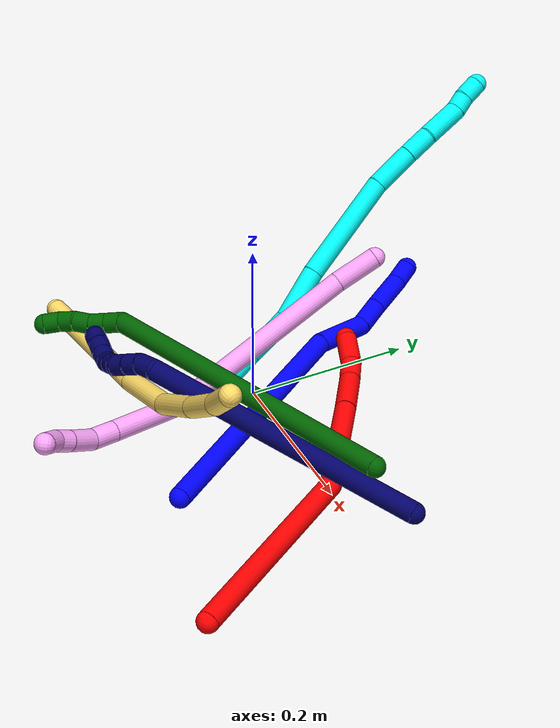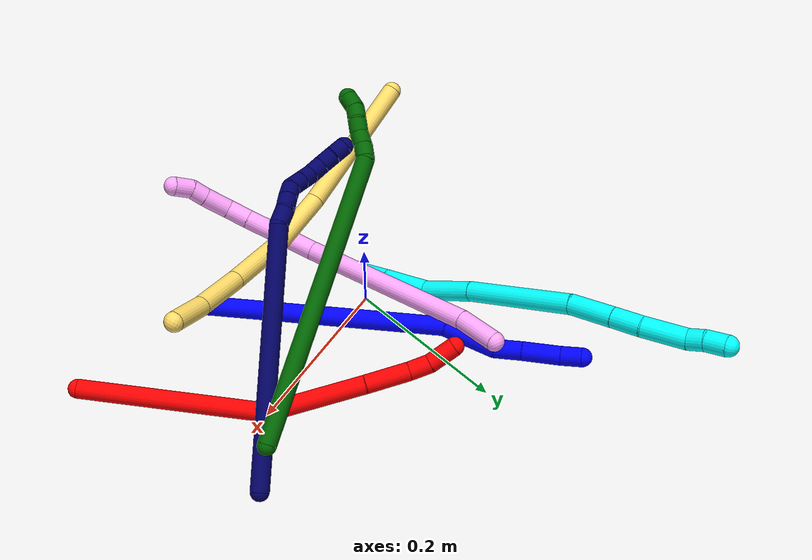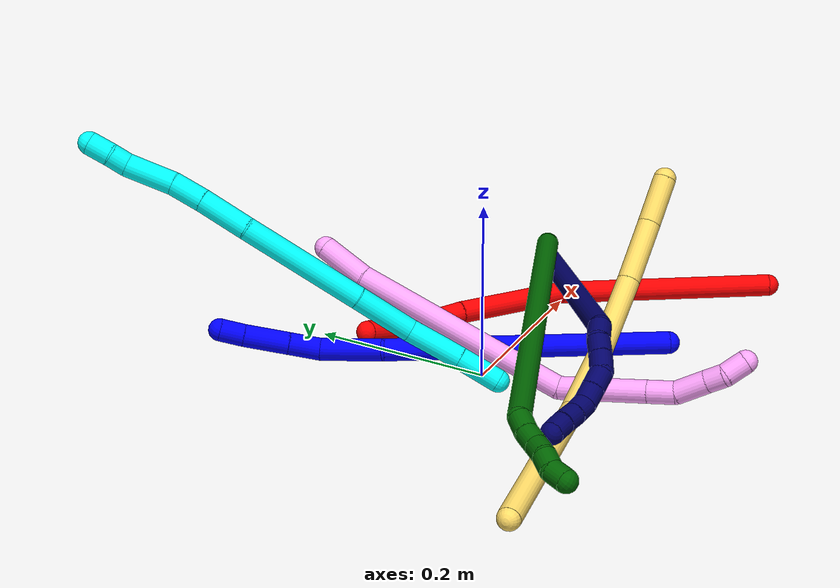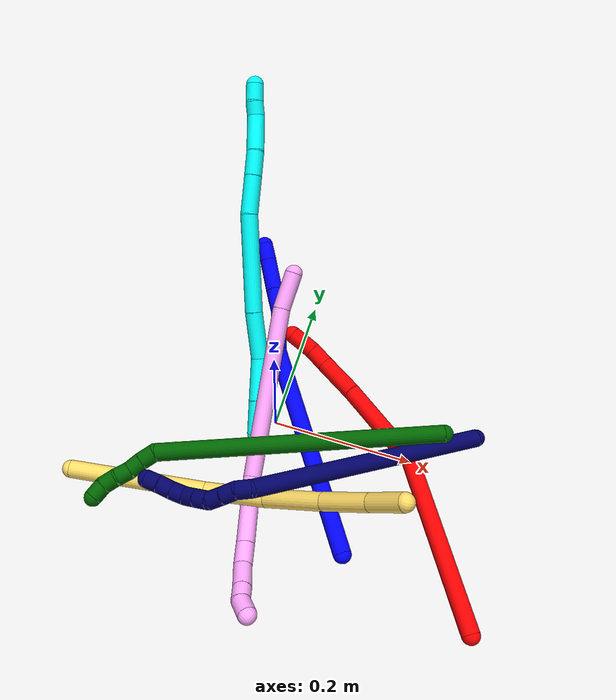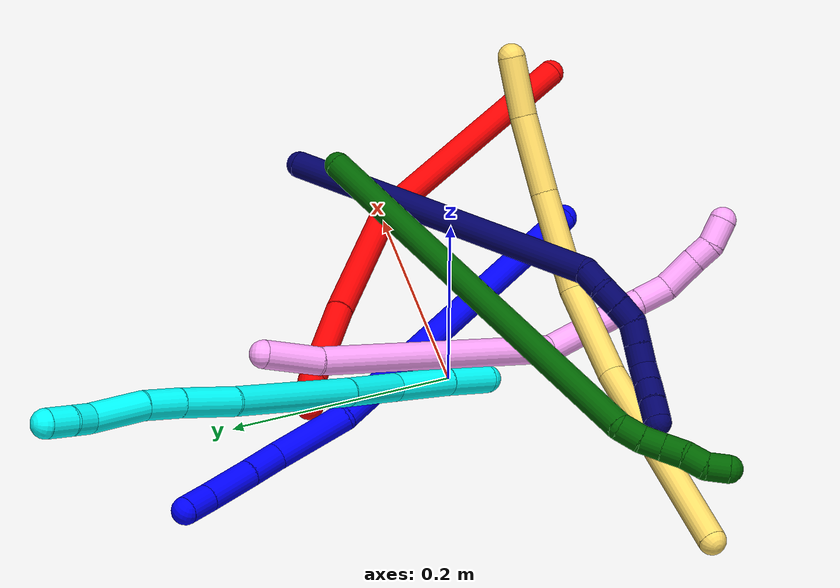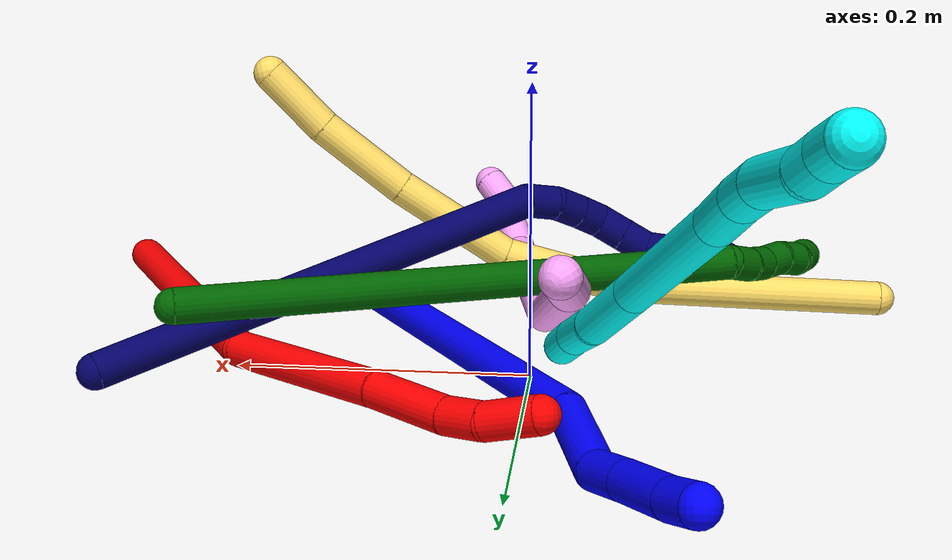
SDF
<sdf version="1.7">
 <world name="default">
  <plugin name="TubeGeneratorPlugin" filename="libtube_generator_plugin.so"/>
  <model name="photoneo_s_sensor">
   <static>1</static>
   <pose>0 0 2 1.57079 1.57079 3.14159</pose>
   <link name="link">
    <inertial><mass>0.1</mass></inertial>
    <sensor name="sensor" type="depth">
     <update_rate>30</update_rate>
     <camera>
      <horizontal_fov>1.22</horizontal_fov>
      <image><width>1920</width><height>1200</height><format>B8G8R8</format></image>
      <clip><near>0.1</near><far>4</far></clip>
      <depth_camera><output>points</output></depth_camera>
     </camera>
     <plugin name="camera_plugin" filename="libgazebo_ros_depth_camera.so">
      <baseline>0.2</baseline>
      <alwaysOn>1</alwaysOn>
      <updateRate>0.0</updateRate>
      <cameraName>camera_ir</cameraName>
      <imageTopicName>/camera/color/image_raw</imageTopicName>
      <cameraInfoTopicName>/camera/color/camera_info</cameraInfoTopicName>
      <depthImageTopicName>/camera/depth/image_raw</depthImageTopicName>
      <depthImageCameraInfoTopicName>/camera/depth/camera_info</depthImageCameraInfoTopicName>
      <pointCloudTopicName>/camera/depth/points</pointCloudTopicName>
      <frameName>fr_optical</frameName>
      <pointCloudCutoff>0.1</pointCloudCutoff>
      <pointCloudCutoffMax>2.0</pointCloudCutoffMax>
      <distortionK1>0</distortionK1>
      <distortionK2>0</distortionK2>
      <distortionK3>0</distortionK3>
      <distortionT1>0</distortionT1>
      <distortionT2>0</distortionT2>
      <CxPrime>0</CxPrime>
      <Cx>0</Cx>
      <Cy>0</Cy>
      <focalLength>0</focalLength>
      <hackBaseline>0</hackBaseline>
     </plugin>
    </sensor>
   </link>
  </model>
  <gravity>0 0 -9.8</gravity>
  <magnetic_field>6e-06 2.3e-05 -4.2e-05</magnetic_field>
  <atmosphere type="adiabatic"/>
  <physics name="default_physics" default="0" type="ode">
   <max_step_size>0.003</max_step_size>
   <real_time_factor>1</real_time_factor>
   <real_time_update_rate>1000</real_time_update_rate>
   <max_contacts>10000</max_contacts>
   <ode>
    <solver>
     <type>quick</type>
     <iters>100</iters>
     <sor>1.3</sor>
     <use_dynamic_moi_rescaling>0</use_dynamic_moi_rescaling>
    </solver>
    <constraints>
     <contact_max_correcting_vel>0</contact_max_correcting_vel>
     <contact_surface_layer>0.001</contact_surface_layer>
     <cfm>0</cfm>
     <erp>0.2</erp>
    </constraints>
   </ode>
  </physics>
  <scene><ambient>0.4 0.4 0.4 1</ambient><background>0.7 0.7 0.7 1</background><shadows>0</shadows></scene>
  <audio><device>default</device></audio>
  <spherical_coordinates>
   <surface_model>EARTH_WGS84</surface_model>
   <latitude_deg>0</latitude_deg>
   <longitude_deg>0</longitude_deg>
   <elevation>0</elevation>
   <heading_deg>0</heading_deg>
  </spherical_coordinates>
  <model name="bin">
   <static>1</static>
   <link name="bottom">
    <collision name="collision-bottom">
     <pose>0 0 -0.01 0 -0 0</pose>
     <geometry><box><size>0.8 0.6 0.02</size></box></geometry>
     <surface>
      <friction><ode><mu>100</mu><mu2>100</mu2></ode></friction>
      <contact><collide_bitmask>65535</collide_bitmask></contact>
     </surface>
    </collision>
   </link>
   <link name="west_wall">
    <collision name="collision-west_wall">
     <pose>-0.41 0 0.1 0 -0 0</pose>
     <geometry><box><size>0.02 0.6 0.2</size></box></geometry>
     <surface>
      <friction><ode><mu>100</mu><mu2>100</mu2></ode></friction>
      <contact><collide_bitmask>65535</collide_bitmask></contact>
     </surface>
    </collision>
   </link>
   <link name="east_wall">
    <collision name="collision-east_wall">
     <pose>0.41 0 0.1 0 -0 0</pose>
     <geometry><box><size>0.02 0.6 0.2</size></box></geometry>
     <surface>
      <friction><ode><mu>100</mu><mu2>100</mu2></ode></friction>
      <contact><collide_bitmask>65535</collide_bitmask></contact>
     </surface>
    </collision>
   </link>
   <link name="south_wall">
    <collision name="collision-south_wall">
     <pose>0 -0.31 0.1 0 -0 0</pose>
     <geometry><box><size>0.8 0.02 0.2</size></box></geometry>
     <surface>
      <friction><ode><mu>100</mu><mu2>100</mu2></ode></friction>
      <contact><collide_bitmask>65535</collide_bitmask></contact>
     </surface>
    </collision>
   </link>
   <link name="north_wall">
    <collision name="collision-north_wall">
     <pose>0 0.31 0.1 0 -0 0</pose>
     <geometry><box><size>0.8 0.02 0.2</size></box></geometry>
     <surface>
      <friction><ode><mu>100</mu><mu2>100</mu2></ode></friction>
      <contact><collide_bitmask>65535</collide_bitmask></contact>
     </surface>
    </collision>
   </link>
  </model>
  <model name="1">
   <static>0</static>
   <link name="1">
    <collision name="collision-cylinder-e_1_1_4">
     <pose>-0.05583 0.138479 0.051851 -1.21252 -0.361018 0.251735</pose>
     <geometry><cylinder><radius>0.0125</radius><length>0.316114</length></cylinder></geometry>
     <surface>
      <friction><ode><mu>1.16</mu><mu2>1.16</mu2><slip1>0</slip1><slip2>0</slip2></ode></friction>
      <contact><ode><kp>1e+06</kp><kd>1</kd><max_vel>0</max_vel><min_depth>0.001</min_depth></ode></contact>
     </surface>
    </collision>
    <visual name="visual-cylinder-e_1_1_4">
     <pose>-0.05583 0.138479 0.051851 -1.21252 -0.361018 0.251735</pose>
     <geometry><cylinder><radius>0.0125</radius><length>0.316114</length></cylinder></geometry>
     <material><ambient>0 0 1 1</ambient></material>
    </visual>
    <collision name="collision-cylinder-e_2_4_5">
     <pose>-0.131385 0.300863 0.121158 -0.940079 -0.587833 0.305145</pose>
     <geometry><cylinder><radius>0.0125</radius><length>0.07114</length></cylinder></geometry>
     <surface>
      <friction><ode><mu>1.16</mu><mu2>1.16</mu2><slip1>0</slip1><slip2>0</slip2></ode></friction>
      <contact><ode><kp>1e+06</kp><kd>1</kd><max_vel>0</max_vel><min_depth>0.001</min_depth></ode></contact>
     </surface>
    </collision>
    <visual name="visual-cylinder-e_2_4_5">
     <pose>-0.131385 0.300863 0.121158 -0.940079 -0.587833 0.305145</pose>
     <geometry><cylinder><radius>0.0125</radius><length>0.07114</length></cylinder></geometry>
     <material><ambient>0 0 1 1</ambient></material>
    </visual>
    <collision name="collision-cylinder-e_3_5_6">
     <pose>-0.159358 0.34055 0.141235 -1.40619 -0.47591 0.405519</pose>
     <geometry><cylinder><radius>0.0125</radius><length>0.036</length></cylinder></geometry>
     <surface>
      <friction><ode><mu>1.16</mu><mu2>1.16</mu2><slip1>0</slip1><slip2>0</slip2></ode></friction>
      <contact><ode><kp>1e+06</kp><kd>1</kd><max_vel>0</max_vel><min_depth>0.001</min_depth></ode></contact>
     </surface>
    </collision>
    <visual name="visual-cylinder-e_3_5_6">
     <pose>-0.159358 0.34055 0.141235 -1.40619 -0.47591 0.405519</pose>
     <geometry><cylinder><radius>0.0125</radius><length>0.036</length></cylinder></geometry>
     <material><ambient>0 0 1 1</ambient></material>
    </visual>
    <collision name="collision-cylinder-e_4_6_7">
     <pose>-0.179499 0.377821 0.148014 -1.37969 -0.497831 0.413452</pose>
     <geometry><cylinder><radius>0.0125</radius><length>0.049818</length></cylinder></geometry>
     <surface>
      <friction><ode><mu>1.16</mu><mu2>1.16</mu2><slip1>0</slip1><slip2>0</slip2></ode></friction>
      <contact><ode><kp>1e+06</kp><kd>1</kd><max_vel>0</max_vel><min_depth>0.001</min_depth></ode></contact>
     </surface>
    </collision>
    <visual name="visual-cylinder-e_4_6_7">
     <pose>-0.179499 0.377821 0.148014 -1.37969 -0.497831 0.413452</pose>
     <geometry><cylinder><radius>0.0125</radius><length>0.049818</length></cylinder></geometry>
     <material><ambient>0 0 1 1</ambient></material>
    </visual>
    <collision name="collision-cylinder-e_5_7_2">
     <pose>-0.1977 0.411143 0.153376 -1.46934 -0.487492 0.441979</pose>
     <geometry><cylinder><radius>0.0125</radius><length>0.026929</length></cylinder></geometry>
     <surface>
      <friction><ode><mu>1.16</mu><mu2>1.16</mu2><slip1>0</slip1><slip2>0</slip2></ode></friction>
      <contact><ode><kp>1e+06</kp><kd>1</kd><max_vel>0</max_vel><min_depth>0.001</min_depth></ode></contact>
     </surface>
    </collision>
    <visual name="visual-cylinder-e_5_7_2">
     <pose>-0.1977 0.411143 0.153376 -1.46934 -0.487492 0.441979</pose>
     <geometry><cylinder><radius>0.0125</radius><length>0.026929</length></cylinder></geometry>
     <material><ambient>0 0 1 1</ambient></material>
    </visual>
    <collision name="collision-sphere-2">
     <pose>-0.204007 0.422978 0.154581 0 -0 0</pose>
     <geometry><sphere><radius>0.0125</radius></sphere></geometry>
     <surface>
      <friction><ode><mu>1.16</mu><mu2>1.16</mu2><slip1>0</slip1><slip2>0</slip2></ode></friction>
      <contact><ode><kp>1e+06</kp><kd>1</kd><max_vel>0</max_vel><min_depth>0.001</min_depth></ode></contact>
     </surface>
    </collision>
    <visual name="visual-sphere-2">
     <pose>-0.204007 0.422978 0.154581 0 -0 0</pose>
     <geometry><sphere><radius>0.0125</radius></sphere></geometry>
     <material><ambient>0 0 1 1</ambient></material>
    </visual>
    <collision name="collision-sphere-7">
     <pose>-0.191393 0.399308 0.152171 0 -0 0</pose>
     <geometry><sphere><radius>0.0125</radius></sphere></geometry>
     <surface>
      <friction><ode><mu>1.16</mu><mu2>1.16</mu2><slip1>0</slip1><slip2>0</slip2></ode></friction>
      <contact><ode><kp>1e+06</kp><kd>1</kd><max_vel>0</max_vel><min_depth>0.001</min_depth></ode></contact>
     </surface>
    </collision>
    <visual name="visual-sphere-7">
     <pose>-0.191393 0.399308 0.152171 0 -0 0</pose>
     <geometry><sphere><radius>0.0125</radius></sphere></geometry>
     <material><ambient>0 0 1 1</ambient></material>
    </visual>
    <collision name="collision-sphere-6">
     <pose>-0.167604 0.356334 0.143857 0 -0 0</pose>
     <geometry><sphere><radius>0.0125</radius></sphere></geometry>
     <surface>
      <friction><ode><mu>1.16</mu><mu2>1.16</mu2><slip1>0</slip1><slip2>0</slip2></ode></friction>
      <contact><ode><kp>1e+06</kp><kd>1</kd><max_vel>0</max_vel><min_depth>0.001</min_depth></ode></contact>
     </surface>
    </collision>
    <visual name="visual-sphere-6">
     <pose>-0.167604 0.356334 0.143857 0 -0 0</pose>
     <geometry><sphere><radius>0.0125</radius></sphere></geometry>
     <material><ambient>0 0 1 1</ambient></material>
    </visual>
    <collision name="collision-sphere-5">
     <pose>-0.151111 0.324767 0.138613 0 -0 0</pose>
     <geometry><sphere><radius>0.0125</radius></sphere></geometry>
     <surface>
      <friction><ode><mu>1.16</mu><mu2>1.16</mu2><slip1>0</slip1><slip2>0</slip2></ode></friction>
      <contact><ode><kp>1e+06</kp><kd>1</kd><max_vel>0</max_vel><min_depth>0.001</min_depth></ode></contact>
     </surface>
    </collision>
    <visual name="visual-sphere-5">
     <pose>-0.151111 0.324767 0.138613 0 -0 0</pose>
     <geometry><sphere><radius>0.0125</radius></sphere></geometry>
     <material><ambient>0 0 1 1</ambient></material>
    </visual>
    <collision name="collision-sphere-1">
     <geometry><sphere><radius>0.0125</radius></sphere></geometry>
     <surface>
      <friction><ode><mu>1.16</mu><mu2>1.16</mu2><slip1>0</slip1><slip2>0</slip2></ode></friction>
      <contact><ode><kp>1e+06</kp><kd>1</kd><max_vel>0</max_vel><min_depth>0.001</min_depth></ode></contact>
     </surface>
    </collision>
    <visual name="visual-sphere-1">
     <geometry><sphere><radius>0.0125</radius></sphere></geometry>
     <material><ambient>0 0 1 1</ambient></material>
    </visual>
    <collision name="collision-sphere-4">
     <pose>-0.11166 0.276958 0.103702 0 -0 0</pose>
     <geometry><sphere><radius>0.0125</radius></sphere></geometry>
     <surface>
      <friction><ode><mu>1.16</mu><mu2>1.16</mu2><slip1>0</slip1><slip2>0</slip2></ode></friction>
      <contact><ode><kp>1e+06</kp><kd>1</kd><max_vel>0</max_vel><min_depth>0.001</min_depth></ode></contact>
     </surface>
    </collision>
    <visual name="visual-sphere-4">
     <pose>-0.11166 0.276958 0.103702 0 -0 0</pose>
     <geometry><sphere><radius>0.0125</radius></sphere></geometry>
     <material><ambient>0 0 1 1</ambient></material>
    </visual>
    <inertial>
     <pose>-0.093997 0.214664 0.083197 0 -0 0</pose>
     <mass>0.5</mass>
     <inertia>
      <ixx>0.003054</ixx>
      <ixy>0</ixy>
      <ixz>0</ixz>
      <iyy>0.001811</iyy>
      <iyz>0</iyz>
      <izz>-0.001383</izz>
     </inertia>
    </inertial>
   </link>
   <pose>0.144233 -0.157675 0.012123 2.89393 0.345631 -2.1791</pose>
  </model>
  <model name="2">
   <static>0</static>
   <link name="2">
    <collision name="collision-cylinder-e_1_1_4">
     <pose>-0.093471 0.075642 -0.018776 -1.81411 -0.875776 1.07883</pose>
     <geometry><cylinder><radius>0.0125</radius><length>0.243402</length></cylinder></geometry>
     <surface>
      <friction><ode><mu>1.16</mu><mu2>1.16</mu2><slip1>0</slip1><slip2>0</slip2></ode></friction>
      <contact><ode><kp>1e+06</kp><kd>1</kd><max_vel>0</max_vel><min_depth>0.001</min_depth></ode></contact>
     </surface>
    </collision>
    <visual name="visual-cylinder-e_1_1_4">
     <pose>-0.093471 0.075642 -0.018776 -1.81411 -0.875776 1.07883</pose>
     <geometry><cylinder><radius>0.0125</radius><length>0.243402</length></cylinder></geometry>
     <material><ambient>1 0 0 1</ambient></material>
    </visual>
    <collision name="collision-cylinder-e_2_4_5">
     <pose>-0.232215 0.183429 -0.071647 -2.38561 -0.768189 1.58848</pose>
     <geometry><cylinder><radius>0.0125</radius><length>0.130312</length></cylinder></geometry>
     <surface>
      <friction><ode><mu>1.16</mu><mu2>1.16</mu2><slip1>0</slip1><slip2>0</slip2></ode></friction>
      <contact><ode><kp>1e+06</kp><kd>1</kd><max_vel>0</max_vel><min_depth>0.001</min_depth></ode></contact>
     </surface>
    </collision>
    <visual name="visual-cylinder-e_2_4_5">
     <pose>-0.232215 0.183429 -0.071647 -2.38561 -0.768189 1.58848</pose>
     <geometry><cylinder><radius>0.0125</radius><length>0.130312</length></cylinder></geometry>
     <material><ambient>1 0 0 1</ambient></material>
    </visual>
    <collision name="collision-cylinder-e_3_5_6">
     <pose>-0.296247 0.23157 -0.122098 -2.36734 -0.686795 1.43995</pose>
     <geometry><cylinder><radius>0.0125</radius><length>0.059172</length></cylinder></geometry>
     <surface>
      <friction><ode><mu>1.16</mu><mu2>1.16</mu2><slip1>0</slip1><slip2>0</slip2></ode></friction>
      <contact><ode><kp>1e+06</kp><kd>1</kd><max_vel>0</max_vel><min_depth>0.001</min_depth></ode></contact>
     </surface>
    </collision>
    <visual name="visual-cylinder-e_3_5_6">
     <pose>-0.296247 0.23157 -0.122098 -2.36734 -0.686795 1.43995</pose>
     <geometry><cylinder><radius>0.0125</radius><length>0.059172</length></cylinder></geometry>
     <material><ambient>1 0 0 1</ambient></material>
    </visual>
    <collision name="collision-cylinder-e_4_6_7">
     <pose>-0.325308 0.253346 -0.146758 -2.53347 -0.794404 1.85713</pose>
     <geometry><cylinder><radius>0.0125</radius><length>0.028879</length></cylinder></geometry>
     <surface>
      <friction><ode><mu>1.16</mu><mu2>1.16</mu2><slip1>0</slip1><slip2>0</slip2></ode></friction>
      <contact><ode><kp>1e+06</kp><kd>1</kd><max_vel>0</max_vel><min_depth>0.001</min_depth></ode></contact>
     </surface>
    </collision>
    <visual name="visual-cylinder-e_4_6_7">
     <pose>-0.325308 0.253346 -0.146758 -2.53347 -0.794404 1.85713</pose>
     <geometry><cylinder><radius>0.0125</radius><length>0.028879</length></cylinder></geometry>
     <material><ambient>1 0 0 1</ambient></material>
    </visual>
    <collision name="collision-cylinder-e_5_7_2">
     <pose>-0.348696 0.262278 -0.168638 -2.91351 -0.753891 2.57832</pose>
     <geometry><cylinder><radius>0.0125</radius><length>0.038235</length></cylinder></geometry>
     <surface>
      <friction><ode><mu>1.16</mu><mu2>1.16</mu2><slip1>0</slip1><slip2>0</slip2></ode></friction>
      <contact><ode><kp>1e+06</kp><kd>1</kd><max_vel>0</max_vel><min_depth>0.001</min_depth></ode></contact>
     </surface>
    </collision>
    <visual name="visual-cylinder-e_5_7_2">
     <pose>-0.348696 0.262278 -0.168638 -2.91351 -0.753891 2.57832</pose>
     <geometry><cylinder><radius>0.0125</radius><length>0.038235</length></cylinder></geometry>
     <material><ambient>1 0 0 1</ambient></material>
    </visual>
    <collision name="collision-sphere-2">
     <pose>-0.361781 0.26543 -0.182215 0 -0 0</pose>
     <geometry><sphere><radius>0.0125</radius></sphere></geometry>
     <surface>
      <friction><ode><mu>1.16</mu><mu2>1.16</mu2><slip1>0</slip1><slip2>0</slip2></ode></friction>
      <contact><ode><kp>1e+06</kp><kd>1</kd><max_vel>0</max_vel><min_depth>0.001</min_depth></ode></contact>
     </surface>
    </collision>
    <visual name="visual-sphere-2">
     <pose>-0.361781 0.26543 -0.182215 0 -0 0</pose>
     <geometry><sphere><radius>0.0125</radius></sphere></geometry>
     <material><ambient>1 0 0 1</ambient></material>
    </visual>
    <collision name="collision-sphere-7">
     <pose>-0.33561 0.259127 -0.155062 0 -0 0</pose>
     <geometry><sphere><radius>0.0125</radius></sphere></geometry>
     <surface>
      <friction><ode><mu>1.16</mu><mu2>1.16</mu2><slip1>0</slip1><slip2>0</slip2></ode></friction>
      <contact><ode><kp>1e+06</kp><kd>1</kd><max_vel>0</max_vel><min_depth>0.001</min_depth></ode></contact>
     </surface>
    </collision>
    <visual name="visual-sphere-7">
     <pose>-0.33561 0.259127 -0.155062 0 -0 0</pose>
     <geometry><sphere><radius>0.0125</radius></sphere></geometry>
     <material><ambient>1 0 0 1</ambient></material>
    </visual>
    <collision name="collision-sphere-6">
     <pose>-0.315006 0.247566 -0.138454 0 -0 0</pose>
     <geometry><sphere><radius>0.0125</radius></sphere></geometry>
     <surface>
      <friction><ode><mu>1.16</mu><mu2>1.16</mu2><slip1>0</slip1><slip2>0</slip2></ode></friction>
      <contact><ode><kp>1e+06</kp><kd>1</kd><max_vel>0</max_vel><min_depth>0.001</min_depth></ode></contact>
     </surface>
    </collision>
    <visual name="visual-sphere-6">
     <pose>-0.315006 0.247566 -0.138454 0 -0 0</pose>
     <geometry><sphere><radius>0.0125</radius></sphere></geometry>
     <material><ambient>1 0 0 1</ambient></material>
    </visual>
    <collision name="collision-sphere-5">
     <pose>-0.277488 0.215573 -0.105741 0 -0 0</pose>
     <geometry><sphere><radius>0.0125</radius></sphere></geometry>
     <surface>
      <friction><ode><mu>1.16</mu><mu2>1.16</mu2><slip1>0</slip1><slip2>0</slip2></ode></friction>
      <contact><ode><kp>1e+06</kp><kd>1</kd><max_vel>0</max_vel><min_depth>0.001</min_depth></ode></contact>
     </surface>
    </collision>
    <visual name="visual-sphere-5">
     <pose>-0.277488 0.215573 -0.105741 0 -0 0</pose>
     <geometry><sphere><radius>0.0125</radius></sphere></geometry>
     <material><ambient>1 0 0 1</ambient></material>
    </visual>
    <collision name="collision-sphere-1">
     <geometry><sphere><radius>0.0125</radius></sphere></geometry>
     <surface>
      <friction><ode><mu>1.16</mu><mu2>1.16</mu2><slip1>0</slip1><slip2>0</slip2></ode></friction>
      <contact><ode><kp>1e+06</kp><kd>1</kd><max_vel>0</max_vel><min_depth>0.001</min_depth></ode></contact>
     </surface>
    </collision>
    <visual name="visual-sphere-1">
     <geometry><sphere><radius>0.0125</radius></sphere></geometry>
     <material><ambient>1 0 0 1</ambient></material>
    </visual>
    <collision name="collision-sphere-4">
     <pose>-0.186942 0.151284 -0.037553 0 -0 0</pose>
     <geometry><sphere><radius>0.0125</radius></sphere></geometry>
     <surface>
      <friction><ode><mu>1.16</mu><mu2>1.16</mu2><slip1>0</slip1><slip2>0</slip2></ode></friction>
      <contact><ode><kp>1e+06</kp><kd>1</kd><max_vel>0</max_vel><min_depth>0.001</min_depth></ode></contact>
     </surface>
    </collision>
    <visual name="visual-sphere-4">
     <pose>-0.186942 0.151284 -0.037553 0 -0 0</pose>
     <geometry><sphere><radius>0.0125</radius></sphere></geometry>
     <material><ambient>1 0 0 1</ambient></material>
    </visual>
    <inertial>
     <pose>-0.186536 0.146723 -0.063635 0 -0 0</pose>
     <mass>0.5</mass>
     <inertia>
      <ixx>0.001173</ixx>
      <ixy>0</ixy>
      <ixz>0</ixz>
      <iyy>0.001625</iyy>
      <iyz>0</iyz>
      <izz>0.000207</izz>
     </inertia>
    </inertial>
   </link>
   <pose>0.327459 -0.20726 0.013709 -1.52382 0.678196 -1.1389</pose>
  </model>
  <model name="3">
   <static>0</static>
   <link name="3">
    <collision name="collision-cylinder-e_1_1_4">
     <pose>-0.000596 0.003073 0.023415 -0.130496 -0.025215 0.001648</pose>
     <geometry><cylinder><radius>0.0125</radius><length>0.047246</length></cylinder></geometry>
     <surface>
      <friction><ode><mu>1.16</mu><mu2>1.16</mu2><slip1>0</slip1><slip2>0</slip2></ode></friction>
      <contact><ode><kp>1e+06</kp><kd>1</kd><max_vel>0</max_vel><min_depth>0.001</min_depth></ode></contact>
     </surface>
    </collision>
    <visual name="visual-cylinder-e_1_1_4">
     <pose>-0.000596 0.003073 0.023415 -0.130496 -0.025215 0.001648</pose>
     <geometry><cylinder><radius>0.0125</radius><length>0.047246</length></cylinder></geometry>
     <material><ambient>0.003922 1 0.996078 1</ambient></material>
    </visual>
    <collision name="collision-cylinder-e_2_4_5">
     <pose>-0.000746 0.009851 0.07711 -0.121752 0.014596 -0.00089</pose>
     <geometry><cylinder><radius>0.0125</radius><length>0.06102</length></cylinder></geometry>
     <surface>
      <friction><ode><mu>1.16</mu><mu2>1.16</mu2><slip1>0</slip1><slip2>0</slip2></ode></friction>
      <contact><ode><kp>1e+06</kp><kd>1</kd><max_vel>0</max_vel><min_depth>0.001</min_depth></ode></contact>
     </surface>
    </collision>
    <visual name="visual-cylinder-e_2_4_5">
     <pose>-0.000746 0.009851 0.07711 -0.121752 0.014596 -0.00089</pose>
     <geometry><cylinder><radius>0.0125</radius><length>0.06102</length></cylinder></geometry>
     <material><ambient>0.003922 1 0.996078 1</ambient></material>
    </visual>
    <collision name="collision-cylinder-e_3_5_6">
     <pose>-0.003994 0.024236 0.138868 -0.327096 -0.110652 0.018278</pose>
     <geometry><cylinder><radius>0.0125</radius><length>0.066889</length></cylinder></geometry>
     <surface>
      <friction><ode><mu>1.16</mu><mu2>1.16</mu2><slip1>0</slip1><slip2>0</slip2></ode></friction>
      <contact><ode><kp>1e+06</kp><kd>1</kd><max_vel>0</max_vel><min_depth>0.001</min_depth></ode></contact>
     </surface>
    </collision>
    <visual name="visual-cylinder-e_3_5_6">
     <pose>-0.003994 0.024236 0.138868 -0.327096 -0.110652 0.018278</pose>
     <geometry><cylinder><radius>0.0125</radius><length>0.066889</length></cylinder></geometry>
     <material><ambient>0.003922 1 0.996078 1</ambient></material>
    </visual>
    <collision name="collision-cylinder-e_4_6_7">
     <pose>-0.013207 0.051167 0.236986 -0.239192 -0.0803 0.009655</pose>
     <geometry><cylinder><radius>0.0125</radius><length>0.13763</length></cylinder></geometry>
     <surface>
      <friction><ode><mu>1.16</mu><mu2>1.16</mu2><slip1>0</slip1><slip2>0</slip2></ode></friction>
      <contact><ode><kp>1e+06</kp><kd>1</kd><max_vel>0</max_vel><min_depth>0.001</min_depth></ode></contact>
     </surface>
    </collision>
    <visual name="visual-cylinder-e_4_6_7">
     <pose>-0.013207 0.051167 0.236986 -0.239192 -0.0803 0.009655</pose>
     <geometry><cylinder><radius>0.0125</radius><length>0.13763</length></cylinder></geometry>
     <material><ambient>0.003922 1 0.996078 1</ambient></material>
    </visual>
    <collision name="collision-cylinder-e_5_7_8">
     <pose>-0.019777 0.069706 0.330764 -0.084118 -0.038562 0.001623</pose>
     <geometry><cylinder><radius>0.0125</radius><length>0.054508</length></cylinder></geometry>
     <surface>
      <friction><ode><mu>1.16</mu><mu2>1.16</mu2><slip1>0</slip1><slip2>0</slip2></ode></friction>
      <contact><ode><kp>1e+06</kp><kd>1</kd><max_vel>0</max_vel><min_depth>0.001</min_depth></ode></contact>
     </surface>
    </collision>
    <visual name="visual-cylinder-e_5_7_8">
     <pose>-0.019777 0.069706 0.330764 -0.084118 -0.038562 0.001623</pose>
     <geometry><cylinder><radius>0.0125</radius><length>0.054508</length></cylinder></geometry>
     <material><ambient>0.003922 1 0.996078 1</ambient></material>
    </visual>
    <collision name="collision-cylinder-e_6_8_9">
     <pose>-0.020743 0.073455 0.37549 -0.082897 0.00484 -0.000201</pose>
     <geometry><cylinder><radius>0.0125</radius><length>0.035299</length></cylinder></geometry>
     <surface>
      <friction><ode><mu>1.16</mu><mu2>1.16</mu2><slip1>0</slip1><slip2>0</slip2></ode></friction>
      <contact><ode><kp>1e+06</kp><kd>1</kd><max_vel>0</max_vel><min_depth>0.001</min_depth></ode></contact>
     </surface>
    </collision>
    <visual name="visual-cylinder-e_6_8_9">
     <pose>-0.020743 0.073455 0.37549 -0.082897 0.00484 -0.000201</pose>
     <geometry><cylinder><radius>0.0125</radius><length>0.035299</length></cylinder></geometry>
     <material><ambient>0.003922 1 0.996078 1</ambient></material>
    </visual>
    <collision name="collision-cylinder-e_7_9_10">
     <pose>-0.017028 0.078424 0.418913 -0.134918 0.138325 -0.00936</pose>
     <geometry><cylinder><radius>0.0125</radius><length>0.052645</length></cylinder></geometry>
     <surface>
      <friction><ode><mu>1.16</mu><mu2>1.16</mu2><slip1>0</slip1><slip2>0</slip2></ode></friction>
      <contact><ode><kp>1e+06</kp><kd>1</kd><max_vel>0</max_vel><min_depth>0.001</min_depth></ode></contact>
     </surface>
    </collision>
    <visual name="visual-cylinder-e_7_9_10">
     <pose>-0.017028 0.078424 0.418913 -0.134918 0.138325 -0.00936</pose>
     <geometry><cylinder><radius>0.0125</radius><length>0.052645</length></cylinder></geometry>
     <material><ambient>0.003922 1 0.996078 1</ambient></material>
    </visual>
    <collision name="collision-cylinder-e_8_10_11">
     <pose>-0.014294 0.084917 0.454368 -0.300986 -0.088682 0.013456</pose>
     <geometry><cylinder><radius>0.0125</radius><length>0.020225</length></cylinder></geometry>
     <surface>
      <friction><ode><mu>1.16</mu><mu2>1.16</mu2><slip1>0</slip1><slip2>0</slip2></ode></friction>
      <contact><ode><kp>1e+06</kp><kd>1</kd><max_vel>0</max_vel><min_depth>0.001</min_depth></ode></contact>
     </surface>
    </collision>
    <visual name="visual-cylinder-e_8_10_11">
     <pose>-0.014294 0.084917 0.454368 -0.300986 -0.088682 0.013456</pose>
     <geometry><cylinder><radius>0.0125</radius><length>0.020225</length></cylinder></geometry>
     <material><ambient>0.003922 1 0.996078 1</ambient></material>
    </visual>
    <collision name="collision-cylinder-e_9_11_2">
     <pose>-0.01517 0.089728 0.47612 -0.149333 0.001622 -0.000121</pose>
     <geometry><cylinder><radius>0.0125</radius><length>0.024538</length></cylinder></geometry>
     <surface>
      <friction><ode><mu>1.16</mu><mu2>1.16</mu2><slip1>0</slip1><slip2>0</slip2></ode></friction>
      <contact><ode><kp>1e+06</kp><kd>1</kd><max_vel>0</max_vel><min_depth>0.001</min_depth></ode></contact>
     </surface>
    </collision>
    <visual name="visual-cylinder-e_9_11_2">
     <pose>-0.01517 0.089728 0.47612 -0.149333 0.001622 -0.000121</pose>
     <geometry><cylinder><radius>0.0125</radius><length>0.024538</length></cylinder></geometry>
     <material><ambient>0.003922 1 0.996078 1</ambient></material>
    </visual>
    <collision name="collision-sphere-2">
     <pose>-0.01515 0.091554 0.488252 0 -0 0</pose>
     <geometry><sphere><radius>0.0125</radius></sphere></geometry>
     <surface>
      <friction><ode><mu>1.16</mu><mu2>1.16</mu2><slip1>0</slip1><slip2>0</slip2></ode></friction>
      <contact><ode><kp>1e+06</kp><kd>1</kd><max_vel>0</max_vel><min_depth>0.001</min_depth></ode></contact>
     </surface>
    </collision>
    <visual name="visual-sphere-2">
     <pose>-0.01515 0.091554 0.488252 0 -0 0</pose>
     <geometry><sphere><radius>0.0125</radius></sphere></geometry>
     <material><ambient>0.003922 1 0.996078 1</ambient></material>
    </visual>
    <collision name="collision-sphere-11">
     <pose>-0.01519 0.087903 0.463988 0 -0 0</pose>
     <geometry><sphere><radius>0.0125</radius></sphere></geometry>
     <surface>
      <friction><ode><mu>1.16</mu><mu2>1.16</mu2><slip1>0</slip1><slip2>0</slip2></ode></friction>
      <contact><ode><kp>1e+06</kp><kd>1</kd><max_vel>0</max_vel><min_depth>0.001</min_depth></ode></contact>
     </surface>
    </collision>
    <visual name="visual-sphere-11">
     <pose>-0.01519 0.087903 0.463988 0 -0 0</pose>
     <geometry><sphere><radius>0.0125</radius></sphere></geometry>
     <material><ambient>0.003922 1 0.996078 1</ambient></material>
    </visual>
    <collision name="collision-sphere-10">
     <pose>-0.013398 0.08193 0.444747 0 -0 0</pose>
     <geometry><sphere><radius>0.0125</radius></sphere></geometry>
     <surface>
      <friction><ode><mu>1.16</mu><mu2>1.16</mu2><slip1>0</slip1><slip2>0</slip2></ode></friction>
      <contact><ode><kp>1e+06</kp><kd>1</kd><max_vel>0</max_vel><min_depth>0.001</min_depth></ode></contact>
     </surface>
    </collision>
    <visual name="visual-sphere-10">
     <pose>-0.013398 0.08193 0.444747 0 -0 0</pose>
     <geometry><sphere><radius>0.0125</radius></sphere></geometry>
     <material><ambient>0.003922 1 0.996078 1</ambient></material>
    </visual>
    <collision name="collision-sphere-9">
     <pose>-0.020657 0.074917 0.393079 0 -0 0</pose>
     <geometry><sphere><radius>0.0125</radius></sphere></geometry>
     <surface>
      <friction><ode><mu>1.16</mu><mu2>1.16</mu2><slip1>0</slip1><slip2>0</slip2></ode></friction>
      <contact><ode><kp>1e+06</kp><kd>1</kd><max_vel>0</max_vel><min_depth>0.001</min_depth></ode></contact>
     </surface>
    </collision>
    <visual name="visual-sphere-9">
     <pose>-0.020657 0.074917 0.393079 0 -0 0</pose>
     <geometry><sphere><radius>0.0125</radius></sphere></geometry>
     <material><ambient>0.003922 1 0.996078 1</ambient></material>
    </visual>
    <collision name="collision-sphere-4">
     <pose>-0.001191 0.006146 0.046829 0 -0 0</pose>
     <geometry><sphere><radius>0.0125</radius></sphere></geometry>
     <surface>
      <friction><ode><mu>1.16</mu><mu2>1.16</mu2><slip1>0</slip1><slip2>0</slip2></ode></friction>
      <contact><ode><kp>1e+06</kp><kd>1</kd><max_vel>0</max_vel><min_depth>0.001</min_depth></ode></contact>
     </surface>
    </collision>
    <visual name="visual-sphere-4">
     <pose>-0.001191 0.006146 0.046829 0 -0 0</pose>
     <geometry><sphere><radius>0.0125</radius></sphere></geometry>
     <material><ambient>0.003922 1 0.996078 1</ambient></material>
    </visual>
    <collision name="collision-sphere-1">
     <geometry><sphere><radius>0.0125</radius></sphere></geometry>
     <surface>
      <friction><ode><mu>1.16</mu><mu2>1.16</mu2><slip1>0</slip1><slip2>0</slip2></ode></friction>
      <contact><ode><kp>1e+06</kp><kd>1</kd><max_vel>0</max_vel><min_depth>0.001</min_depth></ode></contact>
     </surface>
    </collision>
    <visual name="visual-sphere-1">
     <geometry><sphere><radius>0.0125</radius></sphere></geometry>
     <material><ambient>0.003922 1 0.996078 1</ambient></material>
    </visual>
    <collision name="collision-sphere-8">
     <pose>-0.020828 0.071994 0.357902 0 -0 0</pose>
     <geometry><sphere><radius>0.0125</radius></sphere></geometry>
     <surface>
      <friction><ode><mu>1.16</mu><mu2>1.16</mu2><slip1>0</slip1><slip2>0</slip2></ode></friction>
      <contact><ode><kp>1e+06</kp><kd>1</kd><max_vel>0</max_vel><min_depth>0.001</min_depth></ode></contact>
     </surface>
    </collision>
    <visual name="visual-sphere-8">
     <pose>-0.020828 0.071994 0.357902 0 -0 0</pose>
     <geometry><sphere><radius>0.0125</radius></sphere></geometry>
     <material><ambient>0.003922 1 0.996078 1</ambient></material>
    </visual>
    <collision name="collision-sphere-5">
     <pose>-0.000301 0.013556 0.107391 0 -0 0</pose>
     <geometry><sphere><radius>0.0125</radius></sphere></geometry>
     <surface>
      <friction><ode><mu>1.16</mu><mu2>1.16</mu2><slip1>0</slip1><slip2>0</slip2></ode></friction>
      <contact><ode><kp>1e+06</kp><kd>1</kd><max_vel>0</max_vel><min_depth>0.001</min_depth></ode></contact>
     </surface>
    </collision>
    <visual name="visual-sphere-5">
     <pose>-0.000301 0.013556 0.107391 0 -0 0</pose>
     <geometry><sphere><radius>0.0125</radius></sphere></geometry>
     <material><ambient>0.003922 1 0.996078 1</ambient></material>
    </visual>
    <collision name="collision-sphere-6">
     <pose>-0.007687 0.034916 0.170345 0 -0 0</pose>
     <geometry><sphere><radius>0.0125</radius></sphere></geometry>
     <surface>
      <friction><ode><mu>1.16</mu><mu2>1.16</mu2><slip1>0</slip1><slip2>0</slip2></ode></friction>
      <contact><ode><kp>1e+06</kp><kd>1</kd><max_vel>0</max_vel><min_depth>0.001</min_depth></ode></contact>
     </surface>
    </collision>
    <visual name="visual-sphere-6">
     <pose>-0.007687 0.034916 0.170345 0 -0 0</pose>
     <geometry><sphere><radius>0.0125</radius></sphere></geometry>
     <material><ambient>0.003922 1 0.996078 1</ambient></material>
    </visual>
    <collision name="collision-sphere-7">
     <pose>-0.018727 0.067418 0.303626 0 -0 0</pose>
     <geometry><sphere><radius>0.0125</radius></sphere></geometry>
     <surface>
      <friction><ode><mu>1.16</mu><mu2>1.16</mu2><slip1>0</slip1><slip2>0</slip2></ode></friction>
      <contact><ode><kp>1e+06</kp><kd>1</kd><max_vel>0</max_vel><min_depth>0.001</min_depth></ode></contact>
     </surface>
    </collision>
    <visual name="visual-sphere-7">
     <pose>-0.018727 0.067418 0.303626 0 -0 0</pose>
     <geometry><sphere><radius>0.0125</radius></sphere></geometry>
     <material><ambient>0.003922 1 0.996078 1</ambient></material>
    </visual>
    <inertial>
     <pose>-0.011053 0.047699 0.243854 0 -0 0</pose>
     <mass>0.5</mass>
     <inertia>
      <ixx>0.000321</ixx>
      <ixy>0</ixy>
      <ixz>0</ixz>
      <iyy>0.000322</iyy>
      <iyz>0</iyz>
      <izz>-1.2e-05</izz>
     </inertia>
    </inertial>
   </link>
   <pose>-0.019945 -0.029446 0.011494 0.549689 1.05844 2.30162</pose>
  </model>
  <model name="4">
   <static>0</static>
   <link name="4">
    <collision name="collision-cylinder-e_1_1_4">
     <pose>0.015998 0.006719 -0.020377 -2.82308 0.6407 -2.23988</pose>
     <geometry><cylinder><radius>0.0125</radius><length>0.053527</length></cylinder></geometry>
     <surface>
      <friction><ode><mu>1.16</mu><mu2>1.16</mu2><slip1>0</slip1><slip2>0</slip2></ode></friction>
      <contact><ode><kp>1e+06</kp><kd>1</kd><max_vel>0</max_vel><min_depth>0.001</min_depth></ode></contact>
     </surface>
    </collision>
    <visual name="visual-cylinder-e_1_1_4">
     <pose>0.015998 0.006719 -0.020377 -2.82308 0.6407 -2.23988</pose>
     <geometry><cylinder><radius>0.0125</radius><length>0.053527</length></cylinder></geometry>
     <material><ambient>1 0.65098 0.996078 1</ambient></material>
    </visual>
    <collision name="collision-cylinder-e_2_4_5">
     <pose>0.115578 0.027994 -0.125849 -2.97218 0.76921 -2.72804</pose>
     <geometry><cylinder><radius>0.0125</radius><length>0.240325</length></cylinder></geometry>
     <surface>
      <friction><ode><mu>1.16</mu><mu2>1.16</mu2><slip1>0</slip1><slip2>0</slip2></ode></friction>
      <contact><ode><kp>1e+06</kp><kd>1</kd><max_vel>0</max_vel><min_depth>0.001</min_depth></ode></contact>
     </surface>
    </collision>
    <visual name="visual-cylinder-e_2_4_5">
     <pose>0.115578 0.027994 -0.125849 -2.97218 0.76921 -2.72804</pose>
     <geometry><cylinder><radius>0.0125</radius><length>0.240325</length></cylinder></geometry>
     <material><ambient>1 0.65098 0.996078 1</ambient></material>
    </visual>
    <collision name="collision-cylinder-e_3_5_6">
     <pose>0.225351 0.026105 -0.247034 2.71403 0.583692 1.89008</pose>
     <geometry><cylinder><radius>0.0125</radius><length>0.095054</length></cylinder></geometry>
     <surface>
      <friction><ode><mu>1.16</mu><mu2>1.16</mu2><slip1>0</slip1><slip2>0</slip2></ode></friction>
      <contact><ode><kp>1e+06</kp><kd>1</kd><max_vel>0</max_vel><min_depth>0.001</min_depth></ode></contact>
     </surface>
    </collision>
    <visual name="visual-cylinder-e_3_5_6">
     <pose>0.225351 0.026105 -0.247034 2.71403 0.583692 1.89008</pose>
     <geometry><cylinder><radius>0.0125</radius><length>0.095054</length></cylinder></geometry>
     <material><ambient>1 0.65098 0.996078 1</ambient></material>
    </visual>
    <collision name="collision-cylinder-e_4_6_7">
     <pose>0.259605 0.00444 -0.294726 2.71884 0.564688 1.86784</pose>
     <geometry><cylinder><radius>0.0125</radius><length>0.030126</length></cylinder></geometry>
     <surface>
      <friction><ode><mu>1.16</mu><mu2>1.16</mu2><slip1>0</slip1><slip2>0</slip2></ode></friction>
      <contact><ode><kp>1e+06</kp><kd>1</kd><max_vel>0</max_vel><min_depth>0.001</min_depth></ode></contact>
     </surface>
    </collision>
    <visual name="visual-cylinder-e_4_6_7">
     <pose>0.259605 0.00444 -0.294726 2.71884 0.564688 1.86784</pose>
     <geometry><cylinder><radius>0.0125</radius><length>0.030126</length></cylinder></geometry>
     <material><ambient>1 0.65098 0.996078 1</ambient></material>
    </visual>
    <collision name="collision-cylinder-e_5_7_8">
     <pose>0.273644 -0.012577 -0.318191 2.35888 0.343218 0.795276</pose>
     <geometry><cylinder><radius>0.0125</radius><length>0.035529</length></cylinder></geometry>
     <surface>
      <friction><ode><mu>1.16</mu><mu2>1.16</mu2><slip1>0</slip1><slip2>0</slip2></ode></friction>
      <contact><ode><kp>1e+06</kp><kd>1</kd><max_vel>0</max_vel><min_depth>0.001</min_depth></ode></contact>
     </surface>
    </collision>
    <visual name="visual-cylinder-e_5_7_8">
     <pose>0.273644 -0.012577 -0.318191 2.35888 0.343218 0.795276</pose>
     <geometry><cylinder><radius>0.0125</radius><length>0.035529</length></cylinder></geometry>
     <material><ambient>1 0.65098 0.996078 1</ambient></material>
    </visual>
    <collision name="collision-cylinder-e_6_8_9">
     <pose>0.282487 -0.030917 -0.337265 2.40489 0.286102 0.714351</pose>
     <geometry><cylinder><radius>0.0125</radius><length>0.020304</length></cylinder></geometry>
     <surface>
      <friction><ode><mu>1.16</mu><mu2>1.16</mu2><slip1>0</slip1><slip2>0</slip2></ode></friction>
      <contact><ode><kp>1e+06</kp><kd>1</kd><max_vel>0</max_vel><min_depth>0.001</min_depth></ode></contact>
     </surface>
    </collision>
    <visual name="visual-cylinder-e_6_8_9">
     <pose>0.282487 -0.030917 -0.337265 2.40489 0.286102 0.714351</pose>
     <geometry><cylinder><radius>0.0125</radius><length>0.020304</length></cylinder></geometry>
     <material><ambient>1 0.65098 0.996078 1</ambient></material>
    </visual>
    <collision name="collision-cylinder-e_7_9_2">
     <pose>0.290732 -0.047865 -0.349034 1.98348 0.442357 0.662482</pose>
     <geometry><cylinder><radius>0.0125</radius><length>0.025135</length></cylinder></geometry>
     <surface>
      <friction><ode><mu>1.16</mu><mu2>1.16</mu2><slip1>0</slip1><slip2>0</slip2></ode></friction>
      <contact><ode><kp>1e+06</kp><kd>1</kd><max_vel>0</max_vel><min_depth>0.001</min_depth></ode></contact>
     </surface>
    </collision>
    <visual name="visual-cylinder-e_7_9_2">
     <pose>0.290732 -0.047865 -0.349034 1.98348 0.442357 0.662482</pose>
     <geometry><cylinder><radius>0.0125</radius><length>0.025135</length></cylinder></geometry>
     <material><ambient>1 0.65098 0.996078 1</ambient></material>
    </visual>
    <collision name="collision-sphere-2">
     <pose>0.296112 -0.058269 -0.353589 0 -0 0</pose>
     <geometry><sphere><radius>0.0125</radius></sphere></geometry>
     <surface>
      <friction><ode><mu>1.16</mu><mu2>1.16</mu2><slip1>0</slip1><slip2>0</slip2></ode></friction>
      <contact><ode><kp>1e+06</kp><kd>1</kd><max_vel>0</max_vel><min_depth>0.001</min_depth></ode></contact>
     </surface>
    </collision>
    <visual name="visual-sphere-2">
     <pose>0.296112 -0.058269 -0.353589 0 -0 0</pose>
     <geometry><sphere><radius>0.0125</radius></sphere></geometry>
     <material><ambient>1 0.65098 0.996078 1</ambient></material>
    </visual>
    <collision name="collision-sphere-9">
     <pose>0.285352 -0.03746 -0.344479 0 -0 0</pose>
     <geometry><sphere><radius>0.0125</radius></sphere></geometry>
     <surface>
      <friction><ode><mu>1.16</mu><mu2>1.16</mu2><slip1>0</slip1><slip2>0</slip2></ode></friction>
      <contact><ode><kp>1e+06</kp><kd>1</kd><max_vel>0</max_vel><min_depth>0.001</min_depth></ode></contact>
     </surface>
    </collision>
    <visual name="visual-sphere-9">
     <pose>0.285352 -0.03746 -0.344479 0 -0 0</pose>
     <geometry><sphere><radius>0.0125</radius></sphere></geometry>
     <material><ambient>1 0.65098 0.996078 1</ambient></material>
    </visual>
    <collision name="collision-sphere-4">
     <pose>0.031996 0.013438 -0.040753 0 -0 0</pose>
     <geometry><sphere><radius>0.0125</radius></sphere></geometry>
     <surface>
      <friction><ode><mu>1.16</mu><mu2>1.16</mu2><slip1>0</slip1><slip2>0</slip2></ode></friction>
      <contact><ode><kp>1e+06</kp><kd>1</kd><max_vel>0</max_vel><min_depth>0.001</min_depth></ode></contact>
     </surface>
    </collision>
    <visual name="visual-sphere-4">
     <pose>0.031996 0.013438 -0.040753 0 -0 0</pose>
     <geometry><sphere><radius>0.0125</radius></sphere></geometry>
     <material><ambient>1 0.65098 0.996078 1</ambient></material>
    </visual>
    <collision name="collision-sphere-1">
     <geometry><sphere><radius>0.0125</radius></sphere></geometry>
     <surface>
      <friction><ode><mu>1.16</mu><mu2>1.16</mu2><slip1>0</slip1><slip2>0</slip2></ode></friction>
      <contact><ode><kp>1e+06</kp><kd>1</kd><max_vel>0</max_vel><min_depth>0.001</min_depth></ode></contact>
     </surface>
    </collision>
    <visual name="visual-sphere-1">
     <geometry><sphere><radius>0.0125</radius></sphere></geometry>
     <material><ambient>1 0.65098 0.996078 1</ambient></material>
    </visual>
    <collision name="collision-sphere-8">
     <pose>0.279622 -0.024374 -0.330051 0 -0 0</pose>
     <geometry><sphere><radius>0.0125</radius></sphere></geometry>
     <surface>
      <friction><ode><mu>1.16</mu><mu2>1.16</mu2><slip1>0</slip1><slip2>0</slip2></ode></friction>
      <contact><ode><kp>1e+06</kp><kd>1</kd><max_vel>0</max_vel><min_depth>0.001</min_depth></ode></contact>
     </surface>
    </collision>
    <visual name="visual-sphere-8">
     <pose>0.279622 -0.024374 -0.330051 0 -0 0</pose>
     <geometry><sphere><radius>0.0125</radius></sphere></geometry>
     <material><ambient>1 0.65098 0.996078 1</ambient></material>
    </visual>
    <collision name="collision-sphere-5">
     <pose>0.199159 0.042549 -0.210946 0 -0 0</pose>
     <geometry><sphere><radius>0.0125</radius></sphere></geometry>
     <surface>
      <friction><ode><mu>1.16</mu><mu2>1.16</mu2><slip1>0</slip1><slip2>0</slip2></ode></friction>
      <contact><ode><kp>1e+06</kp><kd>1</kd><max_vel>0</max_vel><min_depth>0.001</min_depth></ode></contact>
     </surface>
    </collision>
    <visual name="visual-sphere-5">
     <pose>0.199159 0.042549 -0.210946 0 -0 0</pose>
     <geometry><sphere><radius>0.0125</radius></sphere></geometry>
     <material><ambient>1 0.65098 0.996078 1</ambient></material>
    </visual>
    <collision name="collision-sphere-6">
     <pose>0.251544 0.009661 -0.283122 0 -0 0</pose>
     <geometry><sphere><radius>0.0125</radius></sphere></geometry>
     <surface>
      <friction><ode><mu>1.16</mu><mu2>1.16</mu2><slip1>0</slip1><slip2>0</slip2></ode></friction>
      <contact><ode><kp>1e+06</kp><kd>1</kd><max_vel>0</max_vel><min_depth>0.001</min_depth></ode></contact>
     </surface>
    </collision>
    <visual name="visual-sphere-6">
     <pose>0.251544 0.009661 -0.283122 0 -0 0</pose>
     <geometry><sphere><radius>0.0125</radius></sphere></geometry>
     <material><ambient>1 0.65098 0.996078 1</ambient></material>
    </visual>
    <collision name="collision-sphere-7">
     <pose>0.267666 -0.00078 -0.30633 0 -0 0</pose>
     <geometry><sphere><radius>0.0125</radius></sphere></geometry>
     <surface>
      <friction><ode><mu>1.16</mu><mu2>1.16</mu2><slip1>0</slip1><slip2>0</slip2></ode></friction>
      <contact><ode><kp>1e+06</kp><kd>1</kd><max_vel>0</max_vel><min_depth>0.001</min_depth></ode></contact>
     </surface>
    </collision>
    <visual name="visual-sphere-7">
     <pose>0.267666 -0.00078 -0.30633 0 -0 0</pose>
     <geometry><sphere><radius>0.0125</radius></sphere></geometry>
     <material><ambient>1 0.65098 0.996078 1</ambient></material>
    </visual>
    <inertial>
     <pose>0.161279 0.014849 -0.181243 0 -0 0</pose>
     <mass>0.5</mass>
     <inertia>
      <ixx>-0.001044</ixx>
      <ixy>0</ixy>
      <ixz>0</ixz>
      <iyy>0.000873</iyy>
      <iyz>0</iyz>
      <izz>-0.001006</izz>
     </inertia>
    </inertial>
   </link>
   <pose>-0.029002 0.175744 0.125965 -1.72329 0.557021 -0.558182</pose>
  </model>
  <model name="5">
   <static>0</static>
   <link name="5">
    <collision name="collision-cylinder-e_1_1_4">
     <pose>0.027845 -0.002158 -0.092614 3.1183 0.29198 2.9835</pose>
     <geometry><cylinder><radius>0.0125</radius><length>0.193467</length></cylinder></geometry>
     <surface>
      <friction><ode><mu>1.16</mu><mu2>1.16</mu2><slip1>0</slip1><slip2>0</slip2></ode></friction>
      <contact><ode><kp>1e+06</kp><kd>1</kd><max_vel>0</max_vel><min_depth>0.001</min_depth></ode></contact>
     </surface>
    </collision>
    <visual name="visual-cylinder-e_1_1_4">
     <pose>0.027845 -0.002158 -0.092614 3.1183 0.29198 2.9835</pose>
     <geometry><cylinder><radius>0.0125</radius><length>0.193467</length></cylinder></geometry>
     <material><ambient>1 0.858824 0.4 1</ambient></material>
    </visual>
    <collision name="collision-cylinder-e_2_4_5">
     <pose>0.077197 -0.00615 -0.224 3.0943 0.505995 2.95913</pose>
     <geometry><cylinder><radius>0.0125</radius><length>0.088752</length></cylinder></geometry>
     <surface>
      <friction><ode><mu>1.16</mu><mu2>1.16</mu2><slip1>0</slip1><slip2>0</slip2></ode></friction>
      <contact><ode><kp>1e+06</kp><kd>1</kd><max_vel>0</max_vel><min_depth>0.001</min_depth></ode></contact>
     </surface>
    </collision>
    <visual name="visual-cylinder-e_2_4_5">
     <pose>0.077197 -0.00615 -0.224 3.0943 0.505995 2.95913</pose>
     <geometry><cylinder><radius>0.0125</radius><length>0.088752</length></cylinder></geometry>
     <material><ambient>1 0.858824 0.4 1</ambient></material>
    </visual>
    <collision name="collision-cylinder-e_3_5_6">
     <pose>0.132094 -0.011081 -0.294083 3.04306 0.815076 2.91416</pose>
     <geometry><cylinder><radius>0.0125</radius><length>0.091756</length></cylinder></geometry>
     <surface>
      <friction><ode><mu>1.16</mu><mu2>1.16</mu2><slip1>0</slip1><slip2>0</slip2></ode></friction>
      <contact><ode><kp>1e+06</kp><kd>1</kd><max_vel>0</max_vel><min_depth>0.001</min_depth></ode></contact>
     </surface>
    </collision>
    <visual name="visual-cylinder-e_3_5_6">
     <pose>0.132094 -0.011081 -0.294083 3.04306 0.815076 2.91416</pose>
     <geometry><cylinder><radius>0.0125</radius><length>0.091756</length></cylinder></geometry>
     <material><ambient>1 0.858824 0.4 1</ambient></material>
    </visual>
    <collision name="collision-cylinder-e_4_6_7">
     <pose>0.193624 -0.016334 -0.347542 3.04443 0.901711 2.94141</pose>
     <geometry><cylinder><radius>0.0125</radius><length>0.071751</length></cylinder></geometry>
     <surface>
      <friction><ode><mu>1.16</mu><mu2>1.16</mu2><slip1>0</slip1><slip2>0</slip2></ode></friction>
      <contact><ode><kp>1e+06</kp><kd>1</kd><max_vel>0</max_vel><min_depth>0.001</min_depth></ode></contact>
     </surface>
    </collision>
    <visual name="visual-cylinder-e_4_6_7">
     <pose>0.193624 -0.016334 -0.347542 3.04443 0.901711 2.94141</pose>
     <geometry><cylinder><radius>0.0125</radius><length>0.071751</length></cylinder></geometry>
     <material><ambient>1 0.858824 0.4 1</ambient></material>
    </visual>
    <collision name="collision-cylinder-e_5_7_2">
     <pose>0.245067 -0.020727 -0.383415 2.98022 1.03277 2.85866</pose>
     <geometry><cylinder><radius>0.0125</radius><length>0.054274</length></cylinder></geometry>
     <surface>
      <friction><ode><mu>1.16</mu><mu2>1.16</mu2><slip1>0</slip1><slip2>0</slip2></ode></friction>
      <contact><ode><kp>1e+06</kp><kd>1</kd><max_vel>0</max_vel><min_depth>0.001</min_depth></ode></contact>
     </surface>
    </collision>
    <visual name="visual-cylinder-e_5_7_2">
     <pose>0.245067 -0.020727 -0.383415 2.98022 1.03277 2.85866</pose>
     <geometry><cylinder><radius>0.0125</radius><length>0.054274</length></cylinder></geometry>
     <material><ambient>1 0.858824 0.4 1</ambient></material>
    </visual>
    <collision name="collision-sphere-2">
     <pose>0.268371 -0.022962 -0.39714 0 -0 0</pose>
     <geometry><sphere><radius>0.0125</radius></sphere></geometry>
     <surface>
      <friction><ode><mu>1.16</mu><mu2>1.16</mu2><slip1>0</slip1><slip2>0</slip2></ode></friction>
      <contact><ode><kp>1e+06</kp><kd>1</kd><max_vel>0</max_vel><min_depth>0.001</min_depth></ode></contact>
     </surface>
    </collision>
    <visual name="visual-sphere-2">
     <pose>0.268371 -0.022962 -0.39714 0 -0 0</pose>
     <geometry><sphere><radius>0.0125</radius></sphere></geometry>
     <material><ambient>1 0.858824 0.4 1</ambient></material>
    </visual>
    <collision name="collision-sphere-7">
     <pose>0.221764 -0.018493 -0.369689 0 -0 0</pose>
     <geometry><sphere><radius>0.0125</radius></sphere></geometry>
     <surface>
      <friction><ode><mu>1.16</mu><mu2>1.16</mu2><slip1>0</slip1><slip2>0</slip2></ode></friction>
      <contact><ode><kp>1e+06</kp><kd>1</kd><max_vel>0</max_vel><min_depth>0.001</min_depth></ode></contact>
     </surface>
    </collision>
    <visual name="visual-sphere-7">
     <pose>0.221764 -0.018493 -0.369689 0 -0 0</pose>
     <geometry><sphere><radius>0.0125</radius></sphere></geometry>
     <material><ambient>1 0.858824 0.4 1</ambient></material>
    </visual>
    <collision name="collision-sphere-6">
     <pose>0.165483 -0.014176 -0.325394 0 -0 0</pose>
     <geometry><sphere><radius>0.0125</radius></sphere></geometry>
     <surface>
      <friction><ode><mu>1.16</mu><mu2>1.16</mu2><slip1>0</slip1><slip2>0</slip2></ode></friction>
      <contact><ode><kp>1e+06</kp><kd>1</kd><max_vel>0</max_vel><min_depth>0.001</min_depth></ode></contact>
     </surface>
    </collision>
    <visual name="visual-sphere-6">
     <pose>0.165483 -0.014176 -0.325394 0 -0 0</pose>
     <geometry><sphere><radius>0.0125</radius></sphere></geometry>
     <material><ambient>1 0.858824 0.4 1</ambient></material>
    </visual>
    <collision name="collision-sphere-5">
     <pose>0.098705 -0.007986 -0.262772 0 -0 0</pose>
     <geometry><sphere><radius>0.0125</radius></sphere></geometry>
     <surface>
      <friction><ode><mu>1.16</mu><mu2>1.16</mu2><slip1>0</slip1><slip2>0</slip2></ode></friction>
      <contact><ode><kp>1e+06</kp><kd>1</kd><max_vel>0</max_vel><min_depth>0.001</min_depth></ode></contact>
     </surface>
    </collision>
    <visual name="visual-sphere-5">
     <pose>0.098705 -0.007986 -0.262772 0 -0 0</pose>
     <geometry><sphere><radius>0.0125</radius></sphere></geometry>
     <material><ambient>1 0.858824 0.4 1</ambient></material>
    </visual>
    <collision name="collision-sphere-1">
     <geometry><sphere><radius>0.0125</radius></sphere></geometry>
     <surface>
      <friction><ode><mu>1.16</mu><mu2>1.16</mu2><slip1>0</slip1><slip2>0</slip2></ode></friction>
      <contact><ode><kp>1e+06</kp><kd>1</kd><max_vel>0</max_vel><min_depth>0.001</min_depth></ode></contact>
     </surface>
    </collision>
    <visual name="visual-sphere-1">
     <geometry><sphere><radius>0.0125</radius></sphere></geometry>
     <material><ambient>1 0.858824 0.4 1</ambient></material>
    </visual>
    <collision name="collision-sphere-4">
     <pose>0.055689 -0.004315 -0.185228 0 -0 0</pose>
     <geometry><sphere><radius>0.0125</radius></sphere></geometry>
     <surface>
      <friction><ode><mu>1.16</mu><mu2>1.16</mu2><slip1>0</slip1><slip2>0</slip2></ode></friction>
      <contact><ode><kp>1e+06</kp><kd>1</kd><max_vel>0</max_vel><min_depth>0.001</min_depth></ode></contact>
     </surface>
    </collision>
    <visual name="visual-sphere-4">
     <pose>0.055689 -0.004315 -0.185228 0 -0 0</pose>
     <geometry><sphere><radius>0.0125</radius></sphere></geometry>
     <material><ambient>1 0.858824 0.4 1</ambient></material>
    </visual>
    <inertial>
     <pose>0.103105 -0.008554 -0.221056 0 -0 0</pose>
     <mass>0.5</mass>
     <inertia>
      <ixx>-0.000565</ixx>
      <ixy>0</ixy>
      <ixz>0</ixz>
      <iyy>0.000897</iyy>
      <iyz>0</iyz>
      <izz>-0.000302</izz>
     </inertia>
    </inertial>
   </link>
   <pose>-0.249131 -0.157349 0.011856 0.171744 -1.33532 -0.019533</pose>
  </model>
  <model name="6">
   <static>0</static>
   <link name="6">
    <collision name="collision-cylinder-e_1_1_4">
     <pose>-0.178353 -0.077156 0.040644 1.08596 -1.11602 -0.720496</pose>
     <geometry><cylinder><radius>0.0125</radius><length>0.397064</length></cylinder></geometry>
     <surface>
      <friction><ode><mu>1.16</mu><mu2>1.16</mu2><slip1>0</slip1><slip2>0</slip2></ode></friction>
      <contact><ode><kp>1e+06</kp><kd>1</kd><max_vel>0</max_vel><min_depth>0.001</min_depth></ode></contact>
     </surface>
    </collision>
    <visual name="visual-cylinder-e_1_1_4">
     <pose>-0.178353 -0.077156 0.040644 1.08596 -1.11602 -0.720496</pose>
     <geometry><cylinder><radius>0.0125</radius><length>0.397064</length></cylinder></geometry>
     <material><ambient>0 0.392157 0.003922 1</ambient></material>
    </visual>
    <collision name="collision-cylinder-e_2_4_5">
     <pose>-0.365967 -0.158929 0.078074 2.17893 -1.02491 -1.64502</pose>
     <geometry><cylinder><radius>0.0125</radius><length>0.02167</length></cylinder></geometry>
     <surface>
      <friction><ode><mu>1.16</mu><mu2>1.16</mu2><slip1>0</slip1><slip2>0</slip2></ode></friction>
      <contact><ode><kp>1e+06</kp><kd>1</kd><max_vel>0</max_vel><min_depth>0.001</min_depth></ode></contact>
     </surface>
    </collision>
    <visual name="visual-cylinder-e_2_4_5">
     <pose>-0.365967 -0.158929 0.078074 2.17893 -1.02491 -1.64502</pose>
     <geometry><cylinder><radius>0.0125</radius><length>0.02167</length></cylinder></geometry>
     <material><ambient>0 0.392157 0.003922 1</ambient></material>
    </visual>
    <collision name="collision-cylinder-e_3_5_6">
     <pose>-0.382937 -0.169257 0.071218 2.13861 -0.849943 -1.38014</pose>
     <geometry><cylinder><radius>0.0125</radius><length>0.020526</length></cylinder></geometry>
     <surface>
      <friction><ode><mu>1.16</mu><mu2>1.16</mu2><slip1>0</slip1><slip2>0</slip2></ode></friction>
      <contact><ode><kp>1e+06</kp><kd>1</kd><max_vel>0</max_vel><min_depth>0.001</min_depth></ode></contact>
     </surface>
    </collision>
    <visual name="visual-cylinder-e_3_5_6">
     <pose>-0.382937 -0.169257 0.071218 2.13861 -0.849943 -1.38014</pose>
     <geometry><cylinder><radius>0.0125</radius><length>0.020526</length></cylinder></geometry>
     <material><ambient>0 0.392157 0.003922 1</ambient></material>
    </visual>
    <collision name="collision-cylinder-e_4_6_7">
     <pose>-0.398237 -0.181466 0.066156 1.78576 -0.851235 -1.02551</pose>
     <geometry><cylinder><radius>0.0125</radius><length>0.020185</length></cylinder></geometry>
     <surface>
      <friction><ode><mu>1.16</mu><mu2>1.16</mu2><slip1>0</slip1><slip2>0</slip2></ode></friction>
      <contact><ode><kp>1e+06</kp><kd>1</kd><max_vel>0</max_vel><min_depth>0.001</min_depth></ode></contact>
     </surface>
    </collision>
    <visual name="visual-cylinder-e_4_6_7">
     <pose>-0.398237 -0.181466 0.066156 1.78576 -0.851235 -1.02551</pose>
     <geometry><cylinder><radius>0.0125</radius><length>0.020185</length></cylinder></geometry>
     <material><ambient>0 0.392157 0.003922 1</ambient></material>
    </visual>
    <collision name="collision-cylinder-e_5_7_8">
     <pose>-0.414379 -0.192566 0.061939 2.1172 -1.00875 -1.5524</pose>
     <geometry><cylinder><radius>0.0125</radius><length>0.020211</length></cylinder></geometry>
     <surface>
      <friction><ode><mu>1.16</mu><mu2>1.16</mu2><slip1>0</slip1><slip2>0</slip2></ode></friction>
      <contact><ode><kp>1e+06</kp><kd>1</kd><max_vel>0</max_vel><min_depth>0.001</min_depth></ode></contact>
     </surface>
    </collision>
    <visual name="visual-cylinder-e_5_7_8">
     <pose>-0.414379 -0.192566 0.061939 2.1172 -1.00875 -1.5524</pose>
     <geometry><cylinder><radius>0.0125</radius><length>0.020211</length></cylinder></geometry>
     <material><ambient>0 0.392157 0.003922 1</ambient></material>
    </visual>
    <collision name="collision-cylinder-e_6_8_2">
     <pose>-0.428705 -0.203875 0.054128 2.2125 -0.603745 -1.11198</pose>
     <geometry><cylinder><radius>0.0125</radius><length>0.020344</length></cylinder></geometry>
     <surface>
      <friction><ode><mu>1.16</mu><mu2>1.16</mu2><slip1>0</slip1><slip2>0</slip2></ode></friction>
      <contact><ode><kp>1e+06</kp><kd>1</kd><max_vel>0</max_vel><min_depth>0.001</min_depth></ode></contact>
     </surface>
    </collision>
    <visual name="visual-cylinder-e_6_8_2">
     <pose>-0.428705 -0.203875 0.054128 2.2125 -0.603745 -1.11198</pose>
     <geometry><cylinder><radius>0.0125</radius><length>0.020344</length></cylinder></geometry>
     <material><ambient>0 0.392157 0.003922 1</ambient></material>
    </visual>
    <collision name="collision-sphere-2">
     <pose>-0.43448 -0.210583 0.049116 0 -0 0</pose>
     <geometry><sphere><radius>0.0125</radius></sphere></geometry>
     <surface>
      <friction><ode><mu>1.16</mu><mu2>1.16</mu2><slip1>0</slip1><slip2>0</slip2></ode></friction>
      <contact><ode><kp>1e+06</kp><kd>1</kd><max_vel>0</max_vel><min_depth>0.001</min_depth></ode></contact>
     </surface>
    </collision>
    <visual name="visual-sphere-2">
     <pose>-0.43448 -0.210583 0.049116 0 -0 0</pose>
     <geometry><sphere><radius>0.0125</radius></sphere></geometry>
     <material><ambient>0 0.392157 0.003922 1</ambient></material>
    </visual>
    <collision name="collision-sphere-4">
     <pose>-0.356707 -0.154313 0.081288 0 -0 0</pose>
     <geometry><sphere><radius>0.0125</radius></sphere></geometry>
     <surface>
      <friction><ode><mu>1.16</mu><mu2>1.16</mu2><slip1>0</slip1><slip2>0</slip2></ode></friction>
      <contact><ode><kp>1e+06</kp><kd>1</kd><max_vel>0</max_vel><min_depth>0.001</min_depth></ode></contact>
     </surface>
    </collision>
    <visual name="visual-sphere-4">
     <pose>-0.356707 -0.154313 0.081288 0 -0 0</pose>
     <geometry><sphere><radius>0.0125</radius></sphere></geometry>
     <material><ambient>0 0.392157 0.003922 1</ambient></material>
    </visual>
    <collision name="collision-sphere-1">
     <geometry><sphere><radius>0.0125</radius></sphere></geometry>
     <surface>
      <friction><ode><mu>1.16</mu><mu2>1.16</mu2><slip1>0</slip1><slip2>0</slip2></ode></friction>
      <contact><ode><kp>1e+06</kp><kd>1</kd><max_vel>0</max_vel><min_depth>0.001</min_depth></ode></contact>
     </surface>
    </collision>
    <visual name="visual-sphere-1">
     <geometry><sphere><radius>0.0125</radius></sphere></geometry>
     <material><ambient>0 0.392157 0.003922 1</ambient></material>
    </visual>
    <collision name="collision-sphere-8">
     <pose>-0.42293 -0.197167 0.05914 0 -0 0</pose>
     <geometry><sphere><radius>0.0125</radius></sphere></geometry>
     <surface>
      <friction><ode><mu>1.16</mu><mu2>1.16</mu2><slip1>0</slip1><slip2>0</slip2></ode></friction>
      <contact><ode><kp>1e+06</kp><kd>1</kd><max_vel>0</max_vel><min_depth>0.001</min_depth></ode></contact>
     </surface>
    </collision>
    <visual name="visual-sphere-8">
     <pose>-0.42293 -0.197167 0.05914 0 -0 0</pose>
     <geometry><sphere><radius>0.0125</radius></sphere></geometry>
     <material><ambient>0 0.392157 0.003922 1</ambient></material>
    </visual>
    <collision name="collision-sphere-5">
     <pose>-0.375227 -0.163546 0.07486 0 -0 0</pose>
     <geometry><sphere><radius>0.0125</radius></sphere></geometry>
     <surface>
      <friction><ode><mu>1.16</mu><mu2>1.16</mu2><slip1>0</slip1><slip2>0</slip2></ode></friction>
      <contact><ode><kp>1e+06</kp><kd>1</kd><max_vel>0</max_vel><min_depth>0.001</min_depth></ode></contact>
     </surface>
    </collision>
    <visual name="visual-sphere-5">
     <pose>-0.375227 -0.163546 0.07486 0 -0 0</pose>
     <geometry><sphere><radius>0.0125</radius></sphere></geometry>
     <material><ambient>0 0.392157 0.003922 1</ambient></material>
    </visual>
    <collision name="collision-sphere-6">
     <pose>-0.390647 -0.174968 0.067575 0 -0 0</pose>
     <geometry><sphere><radius>0.0125</radius></sphere></geometry>
     <surface>
      <friction><ode><mu>1.16</mu><mu2>1.16</mu2><slip1>0</slip1><slip2>0</slip2></ode></friction>
      <contact><ode><kp>1e+06</kp><kd>1</kd><max_vel>0</max_vel><min_depth>0.001</min_depth></ode></contact>
     </surface>
    </collision>
    <visual name="visual-sphere-6">
     <pose>-0.390647 -0.174968 0.067575 0 -0 0</pose>
     <geometry><sphere><radius>0.0125</radius></sphere></geometry>
     <material><ambient>0 0.392157 0.003922 1</ambient></material>
    </visual>
    <collision name="collision-sphere-7">
     <pose>-0.405828 -0.187964 0.064737 0 -0 0</pose>
     <geometry><sphere><radius>0.0125</radius></sphere></geometry>
     <surface>
      <friction><ode><mu>1.16</mu><mu2>1.16</mu2><slip1>0</slip1><slip2>0</slip2></ode></friction>
      <contact><ode><kp>1e+06</kp><kd>1</kd><max_vel>0</max_vel><min_depth>0.001</min_depth></ode></contact>
     </surface>
    </collision>
    <visual name="visual-sphere-7">
     <pose>-0.405828 -0.187964 0.064737 0 -0 0</pose>
     <geometry><sphere><radius>0.0125</radius></sphere></geometry>
     <material><ambient>0 0.392157 0.003922 1</ambient></material>
    </visual>
    <inertial>
     <pose>-0.223487 -0.098513 0.045961 0 -0 0</pose>
     <mass>0.5</mass>
     <inertia>
      <ixx>0.000173</ixx>
      <ixy>0</ixy>
      <ixz>0</ixz>
      <iyy>0.003043</iyy>
      <iyz>0</iyz>
      <izz>0.006748</izz>
     </inertia>
    </inertial>
   </link>
   <pose>0.233207 0.034036 0.053063 -0.808544 -0.445494 0.254426</pose>
  </model>
  <model name="7">
   <static>0</static>
   <link name="7">
    <collision name="collision-cylinder-e_1_1_4">
     <pose>-0.095029 -0.041649 0.131849 0.305962 -0.602129 -0.095677</pose>
     <geometry><cylinder><radius>0.0125</radius><length>0.335555</length></cylinder></geometry>
     <surface>
      <friction><ode><mu>1.16</mu><mu2>1.16</mu2><slip1>0</slip1><slip2>0</slip2></ode></friction>
      <contact><ode><kp>1e+06</kp><kd>1</kd><max_vel>0</max_vel><min_depth>0.001</min_depth></ode></contact>
     </surface>
    </collision>
    <visual name="visual-cylinder-e_1_1_4">
     <pose>-0.095029 -0.041649 0.131849 0.305962 -0.602129 -0.095677</pose>
     <geometry><cylinder><radius>0.0125</radius><length>0.335555</length></cylinder></geometry>
     <material><ambient>0.003922 0 0.403922 1</ambient></material>
    </visual>
    <collision name="collision-cylinder-e_2_4_5">
     <pose>-0.199818 -0.085985 0.268816 0.483538 -1.03609 -0.27927</pose>
     <geometry><cylinder><radius>0.0125</radius><length>0.022687</length></cylinder></geometry>
     <surface>
      <friction><ode><mu>1.16</mu><mu2>1.16</mu2><slip1>0</slip1><slip2>0</slip2></ode></friction>
      <contact><ode><kp>1e+06</kp><kd>1</kd><max_vel>0</max_vel><min_depth>0.001</min_depth></ode></contact>
     </surface>
    </collision>
    <visual name="visual-cylinder-e_2_4_5">
     <pose>-0.199818 -0.085985 0.268816 0.483538 -1.03609 -0.27927</pose>
     <geometry><cylinder><radius>0.0125</radius><length>0.022687</length></cylinder></geometry>
     <material><ambient>0.003922 0 0.403922 1</ambient></material>
    </visual>
    <collision name="collision-cylinder-e_3_5_6">
     <pose>-0.217817 -0.093772 0.276572 1.09346 -0.96211 -0.615175</pose>
     <geometry><cylinder><radius>0.0125</radius><length>0.020085</length></cylinder></geometry>
     <surface>
      <friction><ode><mu>1.16</mu><mu2>1.16</mu2><slip1>0</slip1><slip2>0</slip2></ode></friction>
      <contact><ode><kp>1e+06</kp><kd>1</kd><max_vel>0</max_vel><min_depth>0.001</min_depth></ode></contact>
     </surface>
    </collision>
    <visual name="visual-cylinder-e_3_5_6">
     <pose>-0.217817 -0.093772 0.276572 1.09346 -0.96211 -0.615175</pose>
     <geometry><cylinder><radius>0.0125</radius><length>0.020085</length></cylinder></geometry>
     <material><ambient>0.003922 0 0.403922 1</ambient></material>
    </visual>
    <collision name="collision-cylinder-e_4_6_7">
     <pose>-0.234761 -0.10376 0.281356 1.1569 -1.02074 -0.700925</pose>
     <geometry><cylinder><radius>0.0125</radius><length>0.020422</length></cylinder></geometry>
     <surface>
      <friction><ode><mu>1.16</mu><mu2>1.16</mu2><slip1>0</slip1><slip2>0</slip2></ode></friction>
      <contact><ode><kp>1e+06</kp><kd>1</kd><max_vel>0</max_vel><min_depth>0.001</min_depth></ode></contact>
     </surface>
    </collision>
    <visual name="visual-cylinder-e_4_6_7">
     <pose>-0.234761 -0.10376 0.281356 1.1569 -1.02074 -0.700925</pose>
     <geometry><cylinder><radius>0.0125</radius><length>0.020422</length></cylinder></geometry>
     <material><ambient>0.003922 0 0.403922 1</ambient></material>
    </visual>
    <collision name="collision-cylinder-e_5_7_8">
     <pose>-0.25398 -0.109455 0.283231 1.8951 -1.48982 -1.81734</pose>
     <geometry><cylinder><radius>0.0125</radius><length>0.021098</length></cylinder></geometry>
     <surface>
      <friction><ode><mu>1.16</mu><mu2>1.16</mu2><slip1>0</slip1><slip2>0</slip2></ode></friction>
      <contact><ode><kp>1e+06</kp><kd>1</kd><max_vel>0</max_vel><min_depth>0.001</min_depth></ode></contact>
     </surface>
    </collision>
    <visual name="visual-cylinder-e_5_7_8">
     <pose>-0.25398 -0.109455 0.283231 1.8951 -1.48982 -1.81734</pose>
     <geometry><cylinder><radius>0.0125</radius><length>0.021098</length></cylinder></geometry>
     <material><ambient>0.003922 0 0.403922 1</ambient></material>
    </visual>
    <collision name="collision-cylinder-e_6_8_9">
     <pose>-0.274527 -0.110983 0.28267 1.9531 -1.49368 -1.88051</pose>
     <geometry><cylinder><radius>0.0125</radius><length>0.020124</length></cylinder></geometry>
     <surface>
      <friction><ode><mu>1.16</mu><mu2>1.16</mu2><slip1>0</slip1><slip2>0</slip2></ode></friction>
      <contact><ode><kp>1e+06</kp><kd>1</kd><max_vel>0</max_vel><min_depth>0.001</min_depth></ode></contact>
     </surface>
    </collision>
    <visual name="visual-cylinder-e_6_8_9">
     <pose>-0.274527 -0.110983 0.28267 1.9531 -1.49368 -1.88051</pose>
     <geometry><cylinder><radius>0.0125</radius><length>0.020124</length></cylinder></geometry>
     <material><ambient>0.003922 0 0.403922 1</ambient></material>
    </visual>
    <collision name="collision-cylinder-e_7_9_10">
     <pose>-0.293923 -0.109786 0.28532 -0.57777 -1.21229 0.406347</pose>
     <geometry><cylinder><radius>0.0125</radius><length>0.02</length></cylinder></geometry>
     <surface>
      <friction><ode><mu>1.16</mu><mu2>1.16</mu2><slip1>0</slip1><slip2>0</slip2></ode></friction>
      <contact><ode><kp>1e+06</kp><kd>1</kd><max_vel>0</max_vel><min_depth>0.001</min_depth></ode></contact>
     </surface>
    </collision>
    <visual name="visual-cylinder-e_7_9_10">
     <pose>-0.293923 -0.109786 0.28532 -0.57777 -1.21229 0.406347</pose>
     <geometry><cylinder><radius>0.0125</radius><length>0.02</length></cylinder></geometry>
     <material><ambient>0.003922 0 0.403922 1</ambient></material>
    </visual>
    <collision name="collision-cylinder-e_8_10_11">
     <pose>-0.312369 -0.105212 0.291498 -0.68727 -1.13856 0.450229</pose>
     <geometry><cylinder><radius>0.0125</radius><length>0.020003</length></cylinder></geometry>
     <surface>
      <friction><ode><mu>1.16</mu><mu2>1.16</mu2><slip1>0</slip1><slip2>0</slip2></ode></friction>
      <contact><ode><kp>1e+06</kp><kd>1</kd><max_vel>0</max_vel><min_depth>0.001</min_depth></ode></contact>
     </surface>
    </collision>
    <visual name="visual-cylinder-e_8_10_11">
     <pose>-0.312369 -0.105212 0.291498 -0.68727 -1.13856 0.450229</pose>
     <geometry><cylinder><radius>0.0125</radius><length>0.020003</length></cylinder></geometry>
     <material><ambient>0.003922 0 0.403922 1</ambient></material>
    </visual>
    <collision name="collision-cylinder-e_9_11_2">
     <pose>-0.330893 -0.100517 0.297376 -0.657229 -1.23141 0.473399</pose>
     <geometry><cylinder><radius>0.0125</radius><length>0.020025</length></cylinder></geometry>
     <surface>
      <friction><ode><mu>1.16</mu><mu2>1.16</mu2><slip1>0</slip1><slip2>0</slip2></ode></friction>
      <contact><ode><kp>1e+06</kp><kd>1</kd><max_vel>0</max_vel><min_depth>0.001</min_depth></ode></contact>
     </surface>
    </collision>
    <visual name="visual-cylinder-e_9_11_2">
     <pose>-0.330893 -0.100517 0.297376 -0.657229 -1.23141 0.473399</pose>
     <geometry><cylinder><radius>0.0125</radius><length>0.020025</length></cylinder></geometry>
     <material><ambient>0.003922 0 0.403922 1</ambient></material>
    </visual>
    <collision name="collision-sphere-2">
     <pose>-0.340334 -0.098481 0.300015 0 -0 0</pose>
     <geometry><sphere><radius>0.0125</radius></sphere></geometry>
     <surface>
      <friction><ode><mu>1.16</mu><mu2>1.16</mu2><slip1>0</slip1><slip2>0</slip2></ode></friction>
      <contact><ode><kp>1e+06</kp><kd>1</kd><max_vel>0</max_vel><min_depth>0.001</min_depth></ode></contact>
     </surface>
    </collision>
    <visual name="visual-sphere-2">
     <pose>-0.340334 -0.098481 0.300015 0 -0 0</pose>
     <geometry><sphere><radius>0.0125</radius></sphere></geometry>
     <material><ambient>0.003922 0 0.403922 1</ambient></material>
    </visual>
    <collision name="collision-sphere-11">
     <pose>-0.321451 -0.102553 0.294737 0 -0 0</pose>
     <geometry><sphere><radius>0.0125</radius></sphere></geometry>
     <surface>
      <friction><ode><mu>1.16</mu><mu2>1.16</mu2><slip1>0</slip1><slip2>0</slip2></ode></friction>
      <contact><ode><kp>1e+06</kp><kd>1</kd><max_vel>0</max_vel><min_depth>0.001</min_depth></ode></contact>
     </surface>
    </collision>
    <visual name="visual-sphere-11">
     <pose>-0.321451 -0.102553 0.294737 0 -0 0</pose>
     <geometry><sphere><radius>0.0125</radius></sphere></geometry>
     <material><ambient>0.003922 0 0.403922 1</ambient></material>
    </visual>
    <collision name="collision-sphere-10">
     <pose>-0.303287 -0.10787 0.28826 0 -0 0</pose>
     <geometry><sphere><radius>0.0125</radius></sphere></geometry>
     <surface>
      <friction><ode><mu>1.16</mu><mu2>1.16</mu2><slip1>0</slip1><slip2>0</slip2></ode></friction>
      <contact><ode><kp>1e+06</kp><kd>1</kd><max_vel>0</max_vel><min_depth>0.001</min_depth></ode></contact>
     </surface>
    </collision>
    <visual name="visual-sphere-10">
     <pose>-0.303287 -0.10787 0.28826 0 -0 0</pose>
     <geometry><sphere><radius>0.0125</radius></sphere></geometry>
     <material><ambient>0.003922 0 0.403922 1</ambient></material>
    </visual>
    <collision name="collision-sphere-9">
     <pose>-0.284559 -0.111702 0.282381 0 -0 0</pose>
     <geometry><sphere><radius>0.0125</radius></sphere></geometry>
     <surface>
      <friction><ode><mu>1.16</mu><mu2>1.16</mu2><slip1>0</slip1><slip2>0</slip2></ode></friction>
      <contact><ode><kp>1e+06</kp><kd>1</kd><max_vel>0</max_vel><min_depth>0.001</min_depth></ode></contact>
     </surface>
    </collision>
    <visual name="visual-sphere-9">
     <pose>-0.284559 -0.111702 0.282381 0 -0 0</pose>
     <geometry><sphere><radius>0.0125</radius></sphere></geometry>
     <material><ambient>0.003922 0 0.403922 1</ambient></material>
    </visual>
    <collision name="collision-sphere-4">
     <pose>-0.190058 -0.083297 0.263698 0 -0 0</pose>
     <geometry><sphere><radius>0.0125</radius></sphere></geometry>
     <surface>
      <friction><ode><mu>1.16</mu><mu2>1.16</mu2><slip1>0</slip1><slip2>0</slip2></ode></friction>
      <contact><ode><kp>1e+06</kp><kd>1</kd><max_vel>0</max_vel><min_depth>0.001</min_depth></ode></contact>
     </surface>
    </collision>
    <visual name="visual-sphere-4">
     <pose>-0.190058 -0.083297 0.263698 0 -0 0</pose>
     <geometry><sphere><radius>0.0125</radius></sphere></geometry>
     <material><ambient>0.003922 0 0.403922 1</ambient></material>
    </visual>
    <collision name="collision-sphere-1">
     <geometry><sphere><radius>0.0125</radius></sphere></geometry>
     <surface>
      <friction><ode><mu>1.16</mu><mu2>1.16</mu2><slip1>0</slip1><slip2>0</slip2></ode></friction>
      <contact><ode><kp>1e+06</kp><kd>1</kd><max_vel>0</max_vel><min_depth>0.001</min_depth></ode></contact>
     </surface>
    </collision>
    <visual name="visual-sphere-1">
     <geometry><sphere><radius>0.0125</radius></sphere></geometry>
     <material><ambient>0.003922 0 0.403922 1</ambient></material>
    </visual>
    <collision name="collision-sphere-8">
     <pose>-0.264494 -0.110264 0.282959 0 -0 0</pose>
     <geometry><sphere><radius>0.0125</radius></sphere></geometry>
     <surface>
      <friction><ode><mu>1.16</mu><mu2>1.16</mu2><slip1>0</slip1><slip2>0</slip2></ode></friction>
      <contact><ode><kp>1e+06</kp><kd>1</kd><max_vel>0</max_vel><min_depth>0.001</min_depth></ode></contact>
     </surface>
    </collision>
    <visual name="visual-sphere-8">
     <pose>-0.264494 -0.110264 0.282959 0 -0 0</pose>
     <geometry><sphere><radius>0.0125</radius></sphere></geometry>
     <material><ambient>0.003922 0 0.403922 1</ambient></material>
    </visual>
    <collision name="collision-sphere-5">
     <pose>-0.209578 -0.088672 0.273934 0 -0 0</pose>
     <geometry><sphere><radius>0.0125</radius></sphere></geometry>
     <surface>
      <friction><ode><mu>1.16</mu><mu2>1.16</mu2><slip1>0</slip1><slip2>0</slip2></ode></friction>
      <contact><ode><kp>1e+06</kp><kd>1</kd><max_vel>0</max_vel><min_depth>0.001</min_depth></ode></contact>
     </surface>
    </collision>
    <visual name="visual-sphere-5">
     <pose>-0.209578 -0.088672 0.273934 0 -0 0</pose>
     <geometry><sphere><radius>0.0125</radius></sphere></geometry>
     <material><ambient>0.003922 0 0.403922 1</ambient></material>
    </visual>
    <collision name="collision-sphere-6">
     <pose>-0.226056 -0.098873 0.27921 0 -0 0</pose>
     <geometry><sphere><radius>0.0125</radius></sphere></geometry>
     <surface>
      <friction><ode><mu>1.16</mu><mu2>1.16</mu2><slip1>0</slip1><slip2>0</slip2></ode></friction>
      <contact><ode><kp>1e+06</kp><kd>1</kd><max_vel>0</max_vel><min_depth>0.001</min_depth></ode></contact>
     </surface>
    </collision>
    <visual name="visual-sphere-6">
     <pose>-0.226056 -0.098873 0.27921 0 -0 0</pose>
     <geometry><sphere><radius>0.0125</radius></sphere></geometry>
     <material><ambient>0.003922 0 0.403922 1</ambient></material>
    </visual>
    <collision name="collision-sphere-7">
     <pose>-0.243465 -0.108646 0.283503 0 -0 0</pose>
     <geometry><sphere><radius>0.0125</radius></sphere></geometry>
     <surface>
      <friction><ode><mu>1.16</mu><mu2>1.16</mu2><slip1>0</slip1><slip2>0</slip2></ode></friction>
      <contact><ode><kp>1e+06</kp><kd>1</kd><max_vel>0</max_vel><min_depth>0.001</min_depth></ode></contact>
     </surface>
    </collision>
    <visual name="visual-sphere-7">
     <pose>-0.243465 -0.108646 0.283503 0 -0 0</pose>
     <geometry><sphere><radius>0.0125</radius></sphere></geometry>
     <material><ambient>0.003922 0 0.403922 1</ambient></material>
    </visual>
    <inertial>
     <pose>-0.150452 -0.061569 0.181597 0 -0 0</pose>
     <mass>0.5</mass>
     <inertia>
      <ixx>0.002321</ixx>
      <ixy>0</ixy>
      <ixz>0</ixz>
      <iyy>0.002807</iyy>
      <iyz>0</iyz>
      <izz>0.002611</izz>
     </inertia>
    </inertial>
   </link>
   <pose>0.280115 0.058237 0.014781 0.595865 -0.445606 -0.109661</pose>
  </model>
 </world>
</sdf>
